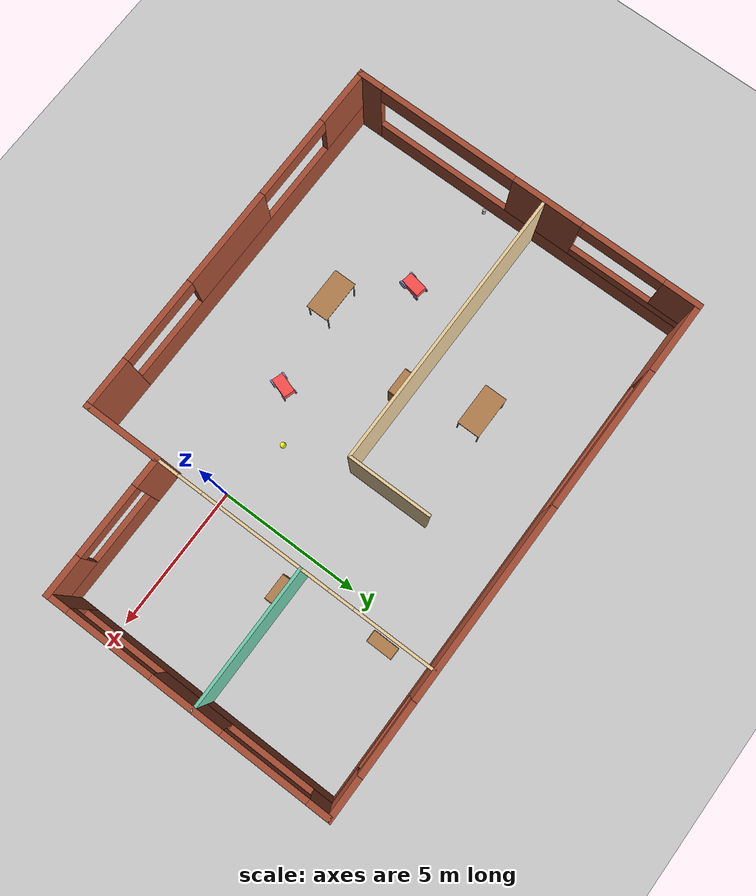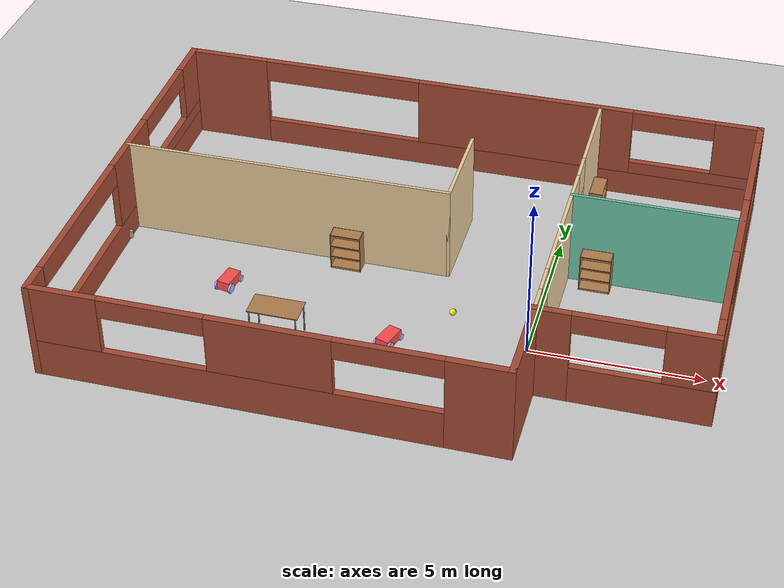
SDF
<sdf version="1.6">
 <world name="default">
  <plugin name="welcome" filename="libwelcome.so"/>
  <light name="sun" type="directional">
   <pose>0 0 10 0 -0 0</pose>
   <diffuse>0.8 0.8 0.8 1</diffuse>
   <specular>0.2 0.2 0.2 1</specular>
   <attenuation>
    <range>1000</range>
    <constant>0.9</constant>
    <linear>0.01</linear>
    <quadratic>0.001</quadratic>
   </attenuation>
   <direction>-0.5 0.1 -0.9</direction>
  </light>
  <model name="ground_plane">
   <static>1</static>
   <link name="link">
    <collision name="collision">
     <geometry><plane><normal>0 0 1</normal><size>100 100</size></plane></geometry>
     <surface>
      <contact><collide_bitmask>65535</collide_bitmask></contact>
      <friction><ode><mu>100</mu><mu2>50</mu2></ode></friction>
     </surface>
    </collision>
    <visual name="visual">
     <cast_shadows>0</cast_shadows>
     <geometry><plane><normal>0 0 1</normal><size>100 100</size></plane></geometry>
     <material>
      <script><uri>file://media/materials/scripts/gazebo.material</uri><name>Gazebo/Grey</name></script>
     </material>
    </visual>
   </link>
  </model>
  <gravity>0 0 -9.8</gravity>
  <magnetic_field>6e-06 2.3e-05 -4.2e-05</magnetic_field>
  <atmosphere type="adiabatic"/>
  <physics name="default_physics" default="0" type="ode">
   <max_step_size>0.001</max_step_size>
   <real_time_factor>1</real_time_factor>
   <real_time_update_rate>1000</real_time_update_rate>
  </physics>
  <scene><ambient>0.4 0.4 0.4 1</ambient><background>0.7 0.7 0.7 1</background><shadows>1</shadows></scene>
  <spherical_coordinates>
   <surface_model>EARTH_WGS84</surface_model>
   <latitude_deg>0</latitude_deg>
   <longitude_deg>0</longitude_deg>
   <elevation>0</elevation>
   <heading_deg>0</heading_deg>
  </spherical_coordinates>
  <model name="bookshelf">
   <static>1</static>
   <link name="link">
    <inertial><mass>1</mass></inertial>
    <collision name="back">
     <pose>0 0.005 0.6 0 -0 0</pose>
     <geometry><box><size>0.9 0.01 1.2</size></box></geometry>
    </collision>
    <visual name="visual1">
     <pose>0 0.005 0.6 0 -0 0</pose>
     <geometry><box><size>0.9 0.01 1.2</size></box></geometry>
     <material>
      <script><uri>file://media/materials/scripts/gazebo.material</uri><name>Gazebo/Wood</name></script>
     </material>
    </visual>
    <collision name="left_side">
     <pose>0.45 -0.195 0.6 0 -0 0</pose>
     <geometry><box><size>0.02 0.4 1.2</size></box></geometry>
    </collision>
    <visual name="visual2">
     <pose>0.45 -0.195 0.6 0 -0 0</pose>
     <geometry><box><size>0.02 0.4 1.2</size></box></geometry>
     <material>
      <script><uri>file://media/materials/scripts/gazebo.material</uri><name>Gazebo/Wood</name></script>
     </material>
    </visual>
    <collision name="right_side">
     <pose>-0.45 -0.195 0.6 0 -0 0</pose>
     <geometry><box><size>0.02 0.4 1.2</size></box></geometry>
    </collision>
    <visual name="visual3">
     <pose>-0.45 -0.195 0.6 0 -0 0</pose>
     <geometry><box><size>0.02 0.4 1.2</size></box></geometry>
     <material>
      <script><uri>file://media/materials/scripts/gazebo.material</uri><name>Gazebo/Wood</name></script>
     </material>
    </visual>
    <collision name="bottom">
     <pose>0 -0.195 0.03 0 -0 0</pose>
     <geometry><box><size>0.88 0.4 0.06</size></box></geometry>
    </collision>
    <visual name="visual4">
     <pose>0 -0.195 0.03 0 -0 0</pose>
     <geometry><box><size>0.88 0.4 0.06</size></box></geometry>
     <material>
      <script><uri>file://media/materials/scripts/gazebo.material</uri><name>Gazebo/Wood</name></script>
     </material>
    </visual>
    <collision name="top">
     <pose>0 -0.195 1.19 0 -0 0</pose>
     <geometry><box><size>0.88 0.4 0.02</size></box></geometry>
    </collision>
    <visual name="visual5">
     <pose>0 -0.195 1.19 0 -0 0</pose>
     <geometry><box><size>0.88 0.4 0.02</size></box></geometry>
     <material>
      <script><uri>file://media/materials/scripts/gazebo.material</uri><name>Gazebo/Wood</name></script>
     </material>
    </visual>
    <collision name="low_shelf">
     <pose>0 -0.195 0.43 0 -0 0</pose>
     <geometry><box><size>0.88 0.4 0.02</size></box></geometry>
    </collision>
    <visual name="visual6">
     <pose>0 -0.195 0.43 0 -0 0</pose>
     <geometry><box><size>0.88 0.4 0.02</size></box></geometry>
     <material>
      <script><uri>file://media/materials/scripts/gazebo.material</uri><name>Gazebo/Wood</name></script>
     </material>
    </visual>
    <collision name="high_shelf">
     <pose>0 -0.195 0.8 0 -0 0</pose>
     <geometry><box><size>0.88 0.4 0.02</size></box></geometry>
    </collision>
    <visual name="visual7">
     <pose>0 -0.195 0.8 0 -0 0</pose>
     <geometry><box><size>0.88 0.4 0.02</size></box></geometry>
     <material>
      <script><uri>file://media/materials/scripts/gazebo.material</uri><name>Gazebo/Wood</name></script>
     </material>
    </visual>
   </link>
   <pose>-5.96108 2.61309 0 0 -0 0</pose>
  </model>
  <model name="beer">
   <link name="link">
    <pose>0 0 0.115 0 -0 0</pose>
    <inertial>
     <mass>0.39</mass>
     <inertia><ixx>0.00058</ixx><ixy>0</ixy><ixz>0</ixz><iyy>0.00058</iyy><iyz>0</iyz><izz>0.00019</izz></inertia>
    </inertial>
    <collision name="collision">
     <geometry><cylinder><radius>0.055</radius><length>0.23</length></cylinder></geometry>
    </collision>
    <visual name="visual">
     <geometry><cylinder><radius>0.055</radius><length>0.23</length></cylinder></geometry>
     <material>
      <script>
       <uri>model://beer/materials/scripts</uri>
       <uri>model://beer/materials/textures</uri>
       <name>Beer/Diffuse</name>
      </script>
     </material>
    </visual>
   </link>
   <pose>-12.2076 1.09427 0.832171 2.9e-05 1.6e-05 0.00079</pose>
  </model>
  <model name="bookshelf_0">
   <static>1</static>
   <link name="link">
    <inertial><mass>1</mass></inertial>
    <collision name="back">
     <pose>0 0.005 0.6 0 -0 0</pose>
     <geometry><box><size>0.9 0.01 1.2</size></box></geometry>
    </collision>
    <visual name="visual1">
     <pose>0 0.005 0.6 0 -0 0</pose>
     <geometry><box><size>0.9 0.01 1.2</size></box></geometry>
     <material>
      <script><uri>file://media/materials/scripts/gazebo.material</uri><name>Gazebo/Wood</name></script>
     </material>
    </visual>
    <collision name="left_side">
     <pose>0.45 -0.195 0.6 0 -0 0</pose>
     <geometry><box><size>0.02 0.4 1.2</size></box></geometry>
    </collision>
    <visual name="visual2">
     <pose>0.45 -0.195 0.6 0 -0 0</pose>
     <geometry><box><size>0.02 0.4 1.2</size></box></geometry>
     <material>
      <script><uri>file://media/materials/scripts/gazebo.material</uri><name>Gazebo/Wood</name></script>
     </material>
    </visual>
    <collision name="right_side">
     <pose>-0.45 -0.195 0.6 0 -0 0</pose>
     <geometry><box><size>0.02 0.4 1.2</size></box></geometry>
    </collision>
    <visual name="visual3">
     <pose>-0.45 -0.195 0.6 0 -0 0</pose>
     <geometry><box><size>0.02 0.4 1.2</size></box></geometry>
     <material>
      <script><uri>file://media/materials/scripts/gazebo.material</uri><name>Gazebo/Wood</name></script>
     </material>
    </visual>
    <collision name="bottom">
     <pose>0 -0.195 0.03 0 -0 0</pose>
     <geometry><box><size>0.88 0.4 0.06</size></box></geometry>
    </collision>
    <visual name="visual4">
     <pose>0 -0.195 0.03 0 -0 0</pose>
     <geometry><box><size>0.88 0.4 0.06</size></box></geometry>
     <material>
      <script><uri>file://media/materials/scripts/gazebo.material</uri><name>Gazebo/Wood</name></script>
     </material>
    </visual>
    <collision name="top">
     <pose>0 -0.195 1.19 0 -0 0</pose>
     <geometry><box><size>0.88 0.4 0.02</size></box></geometry>
    </collision>
    <visual name="visual5">
     <pose>0 -0.195 1.19 0 -0 0</pose>
     <geometry><box><size>0.88 0.4 0.02</size></box></geometry>
     <material>
      <script><uri>file://media/materials/scripts/gazebo.material</uri><name>Gazebo/Wood</name></script>
     </material>
    </visual>
    <collision name="low_shelf">
     <pose>0 -0.195 0.43 0 -0 0</pose>
     <geometry><box><size>0.88 0.4 0.02</size></box></geometry>
    </collision>
    <visual name="visual6">
     <pose>0 -0.195 0.43 0 -0 0</pose>
     <geometry><box><size>0.88 0.4 0.02</size></box></geometry>
     <material>
      <script><uri>file://media/materials/scripts/gazebo.material</uri><name>Gazebo/Wood</name></script>
     </material>
    </visual>
    <collision name="high_shelf">
     <pose>0 -0.195 0.8 0 -0 0</pose>
     <geometry><box><size>0.88 0.4 0.02</size></box></geometry>
    </collision>
    <visual name="visual7">
     <pose>0 -0.195 0.8 0 -0 0</pose>
     <geometry><box><size>0.88 0.4 0.02</size></box></geometry>
     <material>
      <script><uri>file://media/materials/scripts/gazebo.material</uri><name>Gazebo/Wood</name></script>
     </material>
    </visual>
   </link>
   <pose>1.33182 3.46204 0 0 -0 0</pose>
  </model>
  <model name="table">
   <static>1</static>
   <link name="link">
    <collision name="surface">
     <pose>0 0 1 0 -0 0</pose>
     <geometry><box><size>1.5 0.8 0.03</size></box></geometry>
     <surface><friction><ode><mu>0.6</mu><mu2>0.6</mu2></ode></friction></surface>
    </collision>
    <visual name="visual1">
     <pose>0 0 1 0 -0 0</pose>
     <geometry><box><size>1.5 0.8 0.03</size></box></geometry>
     <material>
      <script><uri>file://media/materials/scripts/gazebo.material</uri><name>Gazebo/Wood</name></script>
     </material>
    </visual>
    <collision name="front_left_leg">
     <pose>0.68 0.38 0.5 0 -0 0</pose>
     <geometry><cylinder><radius>0.02</radius><length>1</length></cylinder></geometry>
    </collision>
    <visual name="front_left_leg">
     <pose>0.68 0.38 0.5 0 -0 0</pose>
     <geometry><cylinder><radius>0.02</radius><length>1</length></cylinder></geometry>
     <material>
      <script><uri>file://media/materials/scripts/gazebo.material</uri><name>Gazebo/Grey</name></script>
     </material>
    </visual>
    <collision name="front_right_leg">
     <pose>0.68 -0.38 0.5 0 -0 0</pose>
     <geometry><cylinder><radius>0.02</radius><length>1</length></cylinder></geometry>
    </collision>
    <visual name="front_right_leg">
     <pose>0.68 -0.38 0.5 0 -0 0</pose>
     <geometry><cylinder><radius>0.02</radius><length>1</length></cylinder></geometry>
     <material>
      <script><uri>file://media/materials/scripts/gazebo.material</uri><name>Gazebo/Grey</name></script>
     </material>
    </visual>
    <collision name="back_right_leg">
     <pose>-0.68 -0.38 0.5 0 -0 0</pose>
     <geometry><cylinder><radius>0.02</radius><length>1</length></cylinder></geometry>
    </collision>
    <visual name="back_right_leg">
     <pose>-0.68 -0.38 0.5 0 -0 0</pose>
     <geometry><cylinder><radius>0.02</radius><length>1</length></cylinder></geometry>
     <material>
      <script><uri>file://media/materials/scripts/gazebo.material</uri><name>Gazebo/Grey</name></script>
     </material>
    </visual>
    <collision name="back_left_leg">
     <pose>-0.68 0.38 0.5 0 -0 0</pose>
     <geometry><cylinder><radius>0.02</radius><length>1</length></cylinder></geometry>
    </collision>
    <visual name="back_left_leg">
     <pose>-0.68 0.38 0.5 0 -0 0</pose>
     <geometry><cylinder><radius>0.02</radius><length>1</length></cylinder></geometry>
     <material>
      <script><uri>file://media/materials/scripts/gazebo.material</uri><name>Gazebo/Grey</name></script>
     </material>
    </visual>
   </link>
   <pose>-6.96623 -1.12797 0 0 -0 0</pose>
  </model>
  <model name="bookshelf_1">
   <static>1</static>
   <link name="link">
    <inertial><mass>1</mass></inertial>
    <collision name="back">
     <pose>0 0.005 0.6 0 -0 0</pose>
     <geometry><box><size>0.9 0.01 1.2</size></box></geometry>
    </collision>
    <visual name="visual1">
     <pose>0 0.005 0.6 0 -0 0</pose>
     <geometry><box><size>0.9 0.01 1.2</size></box></geometry>
     <material>
      <script><uri>file://media/materials/scripts/gazebo.material</uri><name>Gazebo/Wood</name></script>
     </material>
    </visual>
    <collision name="left_side">
     <pose>0.45 -0.195 0.6 0 -0 0</pose>
     <geometry><box><size>0.02 0.4 1.2</size></box></geometry>
    </collision>
    <visual name="visual2">
     <pose>0.45 -0.195 0.6 0 -0 0</pose>
     <geometry><box><size>0.02 0.4 1.2</size></box></geometry>
     <material>
      <script><uri>file://media/materials/scripts/gazebo.material</uri><name>Gazebo/Wood</name></script>
     </material>
    </visual>
    <collision name="right_side">
     <pose>-0.45 -0.195 0.6 0 -0 0</pose>
     <geometry><box><size>0.02 0.4 1.2</size></box></geometry>
    </collision>
    <visual name="visual3">
     <pose>-0.45 -0.195 0.6 0 -0 0</pose>
     <geometry><box><size>0.02 0.4 1.2</size></box></geometry>
     <material>
      <script><uri>file://media/materials/scripts/gazebo.material</uri><name>Gazebo/Wood</name></script>
     </material>
    </visual>
    <collision name="bottom">
     <pose>0 -0.195 0.03 0 -0 0</pose>
     <geometry><box><size>0.88 0.4 0.06</size></box></geometry>
    </collision>
    <visual name="visual4">
     <pose>0 -0.195 0.03 0 -0 0</pose>
     <geometry><box><size>0.88 0.4 0.06</size></box></geometry>
     <material>
      <script><uri>file://media/materials/scripts/gazebo.material</uri><name>Gazebo/Wood</name></script>
     </material>
    </visual>
    <collision name="top">
     <pose>0 -0.195 1.19 0 -0 0</pose>
     <geometry><box><size>0.88 0.4 0.02</size></box></geometry>
    </collision>
    <visual name="visual5">
     <pose>0 -0.195 1.19 0 -0 0</pose>
     <geometry><box><size>0.88 0.4 0.02</size></box></geometry>
     <material>
      <script><uri>file://media/materials/scripts/gazebo.material</uri><name>Gazebo/Wood</name></script>
     </material>
    </visual>
    <collision name="low_shelf">
     <pose>0 -0.195 0.43 0 -0 0</pose>
     <geometry><box><size>0.88 0.4 0.02</size></box></geometry>
    </collision>
    <visual name="visual6">
     <pose>0 -0.195 0.43 0 -0 0</pose>
     <geometry><box><size>0.88 0.4 0.02</size></box></geometry>
     <material>
      <script><uri>file://media/materials/scripts/gazebo.material</uri><name>Gazebo/Wood</name></script>
     </material>
    </visual>
    <collision name="high_shelf">
     <pose>0 -0.195 0.8 0 -0 0</pose>
     <geometry><box><size>0.88 0.4 0.02</size></box></geometry>
    </collision>
    <visual name="visual7">
     <pose>0 -0.195 0.8 0 -0 0</pose>
     <geometry><box><size>0.88 0.4 0.02</size></box></geometry>
     <material>
      <script><uri>file://media/materials/scripts/gazebo.material</uri><name>Gazebo/Wood</name></script>
     </material>
    </visual>
   </link>
   <pose>0.564045 6.70754 0 0 -0 1.56615</pose>
  </model>
  <model name="table_0">
   <static>1</static>
   <link name="link">
    <collision name="surface">
     <pose>0 0 1 0 -0 0</pose>
     <geometry><box><size>1.5 0.8 0.03</size></box></geometry>
     <surface><friction><ode><mu>0.6</mu><mu2>0.6</mu2></ode></friction></surface>
    </collision>
    <visual name="visual1">
     <pose>0 0 1 0 -0 0</pose>
     <geometry><box><size>1.5 0.8 0.03</size></box></geometry>
     <material>
      <script><uri>file://media/materials/scripts/gazebo.material</uri><name>Gazebo/Wood</name></script>
     </material>
    </visual>
    <collision name="front_left_leg">
     <pose>0.68 0.38 0.5 0 -0 0</pose>
     <geometry><cylinder><radius>0.02</radius><length>1</length></cylinder></geometry>
    </collision>
    <visual name="front_left_leg">
     <pose>0.68 0.38 0.5 0 -0 0</pose>
     <geometry><cylinder><radius>0.02</radius><length>1</length></cylinder></geometry>
     <material>
      <script><uri>file://media/materials/scripts/gazebo.material</uri><name>Gazebo/Grey</name></script>
     </material>
    </visual>
    <collision name="front_right_leg">
     <pose>0.68 -0.38 0.5 0 -0 0</pose>
     <geometry><cylinder><radius>0.02</radius><length>1</length></cylinder></geometry>
    </collision>
    <visual name="front_right_leg">
     <pose>0.68 -0.38 0.5 0 -0 0</pose>
     <geometry><cylinder><radius>0.02</radius><length>1</length></cylinder></geometry>
     <material>
      <script><uri>file://media/materials/scripts/gazebo.material</uri><name>Gazebo/Grey</name></script>
     </material>
    </visual>
    <collision name="back_right_leg">
     <pose>-0.68 -0.38 0.5 0 -0 0</pose>
     <geometry><cylinder><radius>0.02</radius><length>1</length></cylinder></geometry>
    </collision>
    <visual name="back_right_leg">
     <pose>-0.68 -0.38 0.5 0 -0 0</pose>
     <geometry><cylinder><radius>0.02</radius><length>1</length></cylinder></geometry>
     <material>
      <script><uri>file://media/materials/scripts/gazebo.material</uri><name>Gazebo/Grey</name></script>
     </material>
    </visual>
    <collision name="back_left_leg">
     <pose>-0.68 0.38 0.5 0 -0 0</pose>
     <geometry><cylinder><radius>0.02</radius><length>1</length></cylinder></geometry>
    </collision>
    <visual name="back_left_leg">
     <pose>-0.68 0.38 0.5 0 -0 0</pose>
     <geometry><cylinder><radius>0.02</radius><length>1</length></cylinder></geometry>
     <material>
      <script><uri>file://media/materials/scripts/gazebo.material</uri><name>Gazebo/Grey</name></script>
     </material>
    </visual>
   </link>
   <pose>-6.78918 4.91464 0 0 -0 0</pose>
  </model>
  <model name="Robot">
   <link name="link_0">
    <pose>0 -0.02 0.06 0 -0 0</pose>
    <inertial>
     <mass>1</mass>
     <inertia>
      <ixx>0.166667</ixx>
      <ixy>0</ixy>
      <ixz>0</ixz>
      <iyy>0.166667</iyy>
      <iyz>0</iyz>
      <izz>0.166667</izz>
     </inertia>
    </inertial>
    <visual name="visual">
     <geometry><box><size>0.4 0.7 0.3</size></box></geometry>
     <material>
      <lighting>1</lighting>
      <script><uri>file://media/materials/scripts/gazebo.material</uri><name>Gazebo/Grey</name></script>
      <shader type="pixel"><normal_map>__default__</normal_map></shader>
      <ambient>1 0.3 0.3 1</ambient>
      <diffuse>0.7 0.7 0.7 1</diffuse>
      <specular>0.01 0.01 0.01 1</specular>
      <emissive>0 0 0 1</emissive>
     </material>
    </visual>
    <collision name="collision">
     <geometry><box><size>0.4 0.7 0.3</size></box></geometry>
     <surface>
      <friction>
       <ode><mu>1</mu><mu2>1</mu2><fdir1>0 0 0</fdir1><slip1>0</slip1><slip2>0</slip2></ode>
       <torsional>
        <coefficient>1</coefficient>
        <patch_radius>0</patch_radius>
        <surface_radius>0</surface_radius>
        <use_patch_radius>1</use_patch_radius>
        <ode><slip>0</slip></ode>
       </torsional>
      </friction>
      <bounce><restitution_coefficient>0</restitution_coefficient><threshold>1e+06</threshold></bounce>
      <contact>
       <collide_without_contact>0</collide_without_contact>
       <collide_without_contact_bitmask>1</collide_without_contact_bitmask>
       <collide_bitmask>1</collide_bitmask>
       <ode>
        <soft_cfm>0</soft_cfm>
        <soft_erp>0.2</soft_erp>
        <kp>1e+13</kp>
        <kd>1</kd>
        <max_vel>0.01</max_vel>
        <min_depth>0</min_depth>
       </ode>
       <bullet>
        <split_impulse>1</split_impulse>
        <split_impulse_penetration_threshold>-0.01</split_impulse_penetration_threshold>
        <soft_cfm>0</soft_cfm>
        <soft_erp>0.2</soft_erp>
        <kp>1e+13</kp>
        <kd>1</kd>
       </bullet>
      </contact>
     </surface>
    </collision>
   </link>
   <link name="link_1">
    <pose>-0.215 0.3 -0.04 0 -0 0</pose>
    <inertial>
     <mass>1</mass>
     <inertia><ixx>0.145833</ixx><ixy>0</ixy><ixz>0</ixz><iyy>0.145833</iyy><iyz>0</iyz><izz>0.125</izz></inertia>
    </inertial>
    <visual name="visual">
     <pose>0 0 0 1.5708 -0 1.5708</pose>
     <geometry><cylinder><radius>0.1</radius><length>0.03</length></cylinder></geometry>
     <material>
      <lighting>1</lighting>
      <script><uri>file://media/materials/scripts/gazebo.material</uri><name>Gazebo/Grey</name></script>
      <shader type="pixel"><normal_map>__default__</normal_map></shader>
      <ambient>0.3 0.3 1 1</ambient>
      <diffuse>0.7 0.7 1 1</diffuse>
      <specular>0.01 0.01 0.01 1</specular>
      <emissive>0 0 0 1</emissive>
     </material>
    </visual>
    <collision name="collision">
     <pose>0 0 0 1.5708 -0 1.5708</pose>
     <geometry><cylinder><radius>0.1</radius><length>0.03</length></cylinder></geometry>
     <surface>
      <friction>
       <ode><mu>1</mu><mu2>1</mu2><fdir1>0 0 0</fdir1><slip1>0</slip1><slip2>0</slip2></ode>
       <torsional>
        <coefficient>1</coefficient>
        <patch_radius>0</patch_radius>
        <surface_radius>0</surface_radius>
        <use_patch_radius>1</use_patch_radius>
        <ode><slip>0</slip></ode>
       </torsional>
      </friction>
      <bounce><restitution_coefficient>0</restitution_coefficient><threshold>1e+06</threshold></bounce>
      <contact>
       <collide_without_contact>0</collide_without_contact>
       <collide_without_contact_bitmask>1</collide_without_contact_bitmask>
       <collide_bitmask>1</collide_bitmask>
       <ode>
        <soft_cfm>0</soft_cfm>
        <soft_erp>0.2</soft_erp>
        <kp>1e+13</kp>
        <kd>1</kd>
        <max_vel>0.01</max_vel>
        <min_depth>0</min_depth>
       </ode>
       <bullet>
        <split_impulse>1</split_impulse>
        <split_impulse_penetration_threshold>-0.01</split_impulse_penetration_threshold>
        <soft_cfm>0</soft_cfm>
        <soft_erp>0.2</soft_erp>
        <kp>1e+13</kp>
        <kd>1</kd>
       </bullet>
      </contact>
     </surface>
    </collision>
   </link>
   <link name="link_1_clone">
    <pose>0.215 0.3 -0.04 0 -0 0</pose>
    <inertial>
     <mass>1</mass>
     <inertia><ixx>0.145833</ixx><ixy>0</ixy><ixz>0</ixz><iyy>0.145833</iyy><iyz>0</iyz><izz>0.125</izz></inertia>
    </inertial>
    <visual name="visual">
     <pose>0 0 0 1.5708 -0 1.5708</pose>
     <geometry><cylinder><radius>0.1</radius><length>0.03</length></cylinder></geometry>
     <material>
      <lighting>1</lighting>
      <script><uri>file://media/materials/scripts/gazebo.material</uri><name>Gazebo/Grey</name></script>
      <shader type="pixel"><normal_map>__default__</normal_map></shader>
      <ambient>0.3 0.3 1 1</ambient>
      <diffuse>0.7 0.7 1 1</diffuse>
      <specular>0.01 0.01 0.01 1</specular>
      <emissive>0 0 0 1</emissive>
     </material>
    </visual>
    <collision name="collision">
     <pose>0 0 0 1.5708 -0 1.5708</pose>
     <geometry><cylinder><radius>0.1</radius><length>0.03</length></cylinder></geometry>
     <surface>
      <friction>
       <ode><mu>1</mu><mu2>1</mu2><fdir1>0 0 0</fdir1><slip1>0</slip1><slip2>0</slip2></ode>
       <torsional>
        <coefficient>1</coefficient>
        <patch_radius>0</patch_radius>
        <surface_radius>0</surface_radius>
        <use_patch_radius>1</use_patch_radius>
        <ode><slip>0</slip></ode>
       </torsional>
      </friction>
      <bounce><restitution_coefficient>0</restitution_coefficient><threshold>1e+06</threshold></bounce>
      <contact>
       <collide_without_contact>0</collide_without_contact>
       <collide_without_contact_bitmask>1</collide_without_contact_bitmask>
       <collide_bitmask>1</collide_bitmask>
       <ode>
        <soft_cfm>0</soft_cfm>
        <soft_erp>0.2</soft_erp>
        <kp>1e+13</kp>
        <kd>1</kd>
        <max_vel>0.01</max_vel>
        <min_depth>0</min_depth>
       </ode>
       <bullet>
        <split_impulse>1</split_impulse>
        <split_impulse_penetration_threshold>-0.01</split_impulse_penetration_threshold>
        <soft_cfm>0</soft_cfm>
        <soft_erp>0.2</soft_erp>
        <kp>1e+13</kp>
        <kd>1</kd>
       </bullet>
      </contact>
     </surface>
    </collision>
   </link>
   <link name="link_1_clone_clone">
    <pose>-0.225 -0.29 0.01 0 -0 0</pose>
    <inertial>
     <mass>1</mass>
     <inertia><ixx>0.145833</ixx><ixy>0</ixy><ixz>0</ixz><iyy>0.145833</iyy><iyz>0</iyz><izz>0.125</izz></inertia>
    </inertial>
    <visual name="visual">
     <pose>0 0 0 1.5708 -0 1.5708</pose>
     <geometry><cylinder><radius>0.15</radius><length>0.05</length></cylinder></geometry>
     <material>
      <lighting>1</lighting>
      <script><uri>file://media/materials/scripts/gazebo.material</uri><name>Gazebo/Grey</name></script>
      <shader type="pixel"><normal_map>__default__</normal_map></shader>
      <ambient>0.3 0.3 1 1</ambient>
      <diffuse>0.7 0.7 1 1</diffuse>
      <specular>0.01 0.01 0.01 1</specular>
      <emissive>0 0 0 1</emissive>
     </material>
    </visual>
    <collision name="collision">
     <pose>0 0 0 1.5708 -0 1.5708</pose>
     <geometry><cylinder><radius>0.15</radius><length>0.05</length></cylinder></geometry>
     <surface>
      <friction>
       <ode><mu>1</mu><mu2>1</mu2><fdir1>0 0 0</fdir1><slip1>0</slip1><slip2>0</slip2></ode>
       <torsional>
        <coefficient>1</coefficient>
        <patch_radius>0</patch_radius>
        <surface_radius>0</surface_radius>
        <use_patch_radius>1</use_patch_radius>
        <ode><slip>0</slip></ode>
       </torsional>
      </friction>
      <bounce><restitution_coefficient>0</restitution_coefficient><threshold>1e+06</threshold></bounce>
      <contact>
       <collide_without_contact>0</collide_without_contact>
       <collide_without_contact_bitmask>1</collide_without_contact_bitmask>
       <collide_bitmask>1</collide_bitmask>
       <ode>
        <soft_cfm>0</soft_cfm>
        <soft_erp>0.2</soft_erp>
        <kp>1e+13</kp>
        <kd>1</kd>
        <max_vel>0.01</max_vel>
        <min_depth>0</min_depth>
       </ode>
       <bullet>
        <split_impulse>1</split_impulse>
        <split_impulse_penetration_threshold>-0.01</split_impulse_penetration_threshold>
        <soft_cfm>0</soft_cfm>
        <soft_erp>0.2</soft_erp>
        <kp>1e+13</kp>
        <kd>1</kd>
       </bullet>
      </contact>
     </surface>
    </collision>
   </link>
   <link name="link_1_clone_clone_clone">
    <pose>0.225 -0.29 0.01 0 -0 0</pose>
    <inertial>
     <mass>1</mass>
     <inertia><ixx>0.145833</ixx><ixy>0</ixy><ixz>0</ixz><iyy>0.145833</iyy><iyz>0</iyz><izz>0.125</izz></inertia>
    </inertial>
    <visual name="visual">
     <pose>0 0 0 1.5708 -0 1.5708</pose>
     <geometry><cylinder><radius>0.15</radius><length>0.05</length></cylinder></geometry>
     <material>
      <lighting>1</lighting>
      <script><uri>file://media/materials/scripts/gazebo.material</uri><name>Gazebo/Grey</name></script>
      <shader type="pixel"><normal_map>__default__</normal_map></shader>
      <ambient>0.3 0.3 1 1</ambient>
      <diffuse>0.7 0.7 1 1</diffuse>
      <specular>0.01 0.01 0.01 1</specular>
      <emissive>0 0 0 1</emissive>
     </material>
    </visual>
    <collision name="collision">
     <pose>0 0 0 1.5708 -0 1.5708</pose>
     <geometry><cylinder><radius>0.15</radius><length>0.05</length></cylinder></geometry>
     <surface>
      <friction>
       <ode><mu>1</mu><mu2>1</mu2><fdir1>0 0 0</fdir1><slip1>0</slip1><slip2>0</slip2></ode>
       <torsional>
        <coefficient>1</coefficient>
        <patch_radius>0</patch_radius>
        <surface_radius>0</surface_radius>
        <use_patch_radius>1</use_patch_radius>
        <ode><slip>0</slip></ode>
       </torsional>
      </friction>
      <bounce><restitution_coefficient>0</restitution_coefficient><threshold>1e+06</threshold></bounce>
      <contact>
       <collide_without_contact>0</collide_without_contact>
       <collide_without_contact_bitmask>1</collide_without_contact_bitmask>
       <collide_bitmask>1</collide_bitmask>
       <ode>
        <soft_cfm>0</soft_cfm>
        <soft_erp>0.2</soft_erp>
        <kp>1e+13</kp>
        <kd>1</kd>
        <max_vel>0.01</max_vel>
        <min_depth>0</min_depth>
       </ode>
       <bullet>
        <split_impulse>1</split_impulse>
        <split_impulse_penetration_threshold>-0.01</split_impulse_penetration_threshold>
        <soft_cfm>0</soft_cfm>
        <soft_erp>0.2</soft_erp>
        <kp>1e+13</kp>
        <kd>1</kd>
       </bullet>
      </contact>
     </surface>
    </collision>
   </link>
   <joint name="link_0_JOINT_0" type="revolute">
    <parent>link_0</parent>
    <child>link_1</child>
    <axis>
     <xyz>-1 0 0</xyz>
     <use_parent_model_frame>0</use_parent_model_frame>
     <limit>
      <lower>-1.79769e+308</lower>
      <upper>1.79769e+308</upper>
      <effort>-1</effort>
      <velocity>-1</velocity>
     </limit>
     <dynamics>
      <spring_reference>0</spring_reference>
      <spring_stiffness>0</spring_stiffness>
      <damping>0</damping>
      <friction>0</friction>
     </dynamics>
    </axis>
    <physics>
     <ode><limit><cfm>0</cfm><erp>0.2</erp></limit><suspension><cfm>0</cfm><erp>0.2</erp></suspension></ode>
    </physics>
   </joint>
   <joint name="link_0_JOINT_1" type="revolute">
    <parent>link_0</parent>
    <child>link_1_clone</child>
    <axis>
     <xyz>-1 0 0</xyz>
     <use_parent_model_frame>0</use_parent_model_frame>
     <limit>
      <lower>-1.79769e+308</lower>
      <upper>1.79769e+308</upper>
      <effort>-1</effort>
      <velocity>-1</velocity>
     </limit>
     <dynamics>
      <spring_reference>0</spring_reference>
      <spring_stiffness>0</spring_stiffness>
      <damping>0</damping>
      <friction>0</friction>
     </dynamics>
    </axis>
    <physics>
     <ode><limit><cfm>0</cfm><erp>0.2</erp></limit><suspension><cfm>0</cfm><erp>0.2</erp></suspension></ode>
    </physics>
   </joint>
   <joint name="link_0_JOINT_3" type="revolute">
    <parent>link_0</parent>
    <child>link_1_clone_clone</child>
    <axis>
     <xyz>-1 0 0</xyz>
     <use_parent_model_frame>0</use_parent_model_frame>
     <limit>
      <lower>-1.79769e+308</lower>
      <upper>1.79769e+308</upper>
      <effort>-1</effort>
      <velocity>-1</velocity>
     </limit>
     <dynamics>
      <spring_reference>0</spring_reference>
      <spring_stiffness>0</spring_stiffness>
      <damping>0</damping>
      <friction>0</friction>
     </dynamics>
    </axis>
    <physics>
     <ode><limit><cfm>0</cfm><erp>0.2</erp></limit><suspension><cfm>0</cfm><erp>0.2</erp></suspension></ode>
    </physics>
   </joint>
   <joint name="link_0_JOINT_4" type="revolute">
    <parent>link_0</parent>
    <child>link_1_clone_clone_clone</child>
    <axis>
     <xyz>1 0 0</xyz>
     <use_parent_model_frame>0</use_parent_model_frame>
     <limit>
      <lower>-1.79769e+308</lower>
      <upper>1.79769e+308</upper>
      <effort>-1</effort>
      <velocity>-1</velocity>
     </limit>
     <dynamics>
      <spring_reference>0</spring_reference>
      <spring_stiffness>0</spring_stiffness>
      <damping>0</damping>
      <friction>0</friction>
     </dynamics>
    </axis>
    <physics>
     <ode><limit><cfm>0</cfm><erp>0.2</erp></limit><suspension><cfm>0</cfm><erp>0.2</erp></suspension></ode>
    </physics>
   </joint>
   <static>0</static>
   <pose>-9.03567 0.657132 0.14 0 0 -0.185466</pose>
  </model>
  <model name="Robot_0">
   <link name="link_0">
    <pose>0 -0.02 0.06 0 -0 0</pose>
    <inertial>
     <mass>1</mass>
     <inertia>
      <ixx>0.166667</ixx>
      <ixy>0</ixy>
      <ixz>0</ixz>
      <iyy>0.166667</iyy>
      <iyz>0</iyz>
      <izz>0.166667</izz>
     </inertia>
    </inertial>
    <visual name="visual">
     <geometry><box><size>0.4 0.7 0.3</size></box></geometry>
     <material>
      <lighting>1</lighting>
      <script><uri>file://media/materials/scripts/gazebo.material</uri><name>Gazebo/Grey</name></script>
      <shader type="pixel"><normal_map>__default__</normal_map></shader>
      <ambient>1 0.3 0.3 1</ambient>
      <diffuse>0.7 0.7 0.7 1</diffuse>
      <specular>0.01 0.01 0.01 1</specular>
      <emissive>0 0 0 1</emissive>
     </material>
    </visual>
    <collision name="collision">
     <geometry><box><size>0.4 0.7 0.3</size></box></geometry>
     <surface>
      <friction>
       <ode><mu>1</mu><mu2>1</mu2><fdir1>0 0 0</fdir1><slip1>0</slip1><slip2>0</slip2></ode>
       <torsional>
        <coefficient>1</coefficient>
        <patch_radius>0</patch_radius>
        <surface_radius>0</surface_radius>
        <use_patch_radius>1</use_patch_radius>
        <ode><slip>0</slip></ode>
       </torsional>
      </friction>
      <bounce><restitution_coefficient>0</restitution_coefficient><threshold>1e+06</threshold></bounce>
      <contact>
       <collide_without_contact>0</collide_without_contact>
       <collide_without_contact_bitmask>1</collide_without_contact_bitmask>
       <collide_bitmask>1</collide_bitmask>
       <ode>
        <soft_cfm>0</soft_cfm>
        <soft_erp>0.2</soft_erp>
        <kp>1e+13</kp>
        <kd>1</kd>
        <max_vel>0.01</max_vel>
        <min_depth>0</min_depth>
       </ode>
       <bullet>
        <split_impulse>1</split_impulse>
        <split_impulse_penetration_threshold>-0.01</split_impulse_penetration_threshold>
        <soft_cfm>0</soft_cfm>
        <soft_erp>0.2</soft_erp>
        <kp>1e+13</kp>
        <kd>1</kd>
       </bullet>
      </contact>
     </surface>
    </collision>
   </link>
   <link name="link_1">
    <pose>-0.215 0.3 -0.04 0 -0 0</pose>
    <inertial>
     <mass>1</mass>
     <inertia><ixx>0.145833</ixx><ixy>0</ixy><ixz>0</ixz><iyy>0.145833</iyy><iyz>0</iyz><izz>0.125</izz></inertia>
    </inertial>
    <visual name="visual">
     <pose>0 0 0 1.5708 -0 1.5708</pose>
     <geometry><cylinder><radius>0.1</radius><length>0.03</length></cylinder></geometry>
     <material>
      <lighting>1</lighting>
      <script><uri>file://media/materials/scripts/gazebo.material</uri><name>Gazebo/Grey</name></script>
      <shader type="pixel"><normal_map>__default__</normal_map></shader>
      <ambient>0.3 0.3 1 1</ambient>
      <diffuse>0.7 0.7 1 1</diffuse>
      <specular>0.01 0.01 0.01 1</specular>
      <emissive>0 0 0 1</emissive>
     </material>
    </visual>
    <collision name="collision">
     <pose>0 0 0 1.5708 -0 1.5708</pose>
     <geometry><cylinder><radius>0.1</radius><length>0.03</length></cylinder></geometry>
     <surface>
      <friction>
       <ode><mu>1</mu><mu2>1</mu2><fdir1>0 0 0</fdir1><slip1>0</slip1><slip2>0</slip2></ode>
       <torsional>
        <coefficient>1</coefficient>
        <patch_radius>0</patch_radius>
        <surface_radius>0</surface_radius>
        <use_patch_radius>1</use_patch_radius>
        <ode><slip>0</slip></ode>
       </torsional>
      </friction>
      <bounce><restitution_coefficient>0</restitution_coefficient><threshold>1e+06</threshold></bounce>
      <contact>
       <collide_without_contact>0</collide_without_contact>
       <collide_without_contact_bitmask>1</collide_without_contact_bitmask>
       <collide_bitmask>1</collide_bitmask>
       <ode>
        <soft_cfm>0</soft_cfm>
        <soft_erp>0.2</soft_erp>
        <kp>1e+13</kp>
        <kd>1</kd>
        <max_vel>0.01</max_vel>
        <min_depth>0</min_depth>
       </ode>
       <bullet>
        <split_impulse>1</split_impulse>
        <split_impulse_penetration_threshold>-0.01</split_impulse_penetration_threshold>
        <soft_cfm>0</soft_cfm>
        <soft_erp>0.2</soft_erp>
        <kp>1e+13</kp>
        <kd>1</kd>
       </bullet>
      </contact>
     </surface>
    </collision>
   </link>
   <link name="link_1_clone">
    <pose>0.215 0.3 -0.04 0 -0 0</pose>
    <inertial>
     <mass>1</mass>
     <inertia><ixx>0.145833</ixx><ixy>0</ixy><ixz>0</ixz><iyy>0.145833</iyy><iyz>0</iyz><izz>0.125</izz></inertia>
    </inertial>
    <visual name="visual">
     <pose>0 0 0 1.5708 -0 1.5708</pose>
     <geometry><cylinder><radius>0.1</radius><length>0.03</length></cylinder></geometry>
     <material>
      <lighting>1</lighting>
      <script><uri>file://media/materials/scripts/gazebo.material</uri><name>Gazebo/Grey</name></script>
      <shader type="pixel"><normal_map>__default__</normal_map></shader>
      <ambient>0.3 0.3 1 1</ambient>
      <diffuse>0.7 0.7 1 1</diffuse>
      <specular>0.01 0.01 0.01 1</specular>
      <emissive>0 0 0 1</emissive>
     </material>
    </visual>
    <collision name="collision">
     <pose>0 0 0 1.5708 -0 1.5708</pose>
     <geometry><cylinder><radius>0.1</radius><length>0.03</length></cylinder></geometry>
     <surface>
      <friction>
       <ode><mu>1</mu><mu2>1</mu2><fdir1>0 0 0</fdir1><slip1>0</slip1><slip2>0</slip2></ode>
       <torsional>
        <coefficient>1</coefficient>
        <patch_radius>0</patch_radius>
        <surface_radius>0</surface_radius>
        <use_patch_radius>1</use_patch_radius>
        <ode><slip>0</slip></ode>
       </torsional>
      </friction>
      <bounce><restitution_coefficient>0</restitution_coefficient><threshold>1e+06</threshold></bounce>
      <contact>
       <collide_without_contact>0</collide_without_contact>
       <collide_without_contact_bitmask>1</collide_without_contact_bitmask>
       <collide_bitmask>1</collide_bitmask>
       <ode>
        <soft_cfm>0</soft_cfm>
        <soft_erp>0.2</soft_erp>
        <kp>1e+13</kp>
        <kd>1</kd>
        <max_vel>0.01</max_vel>
        <min_depth>0</min_depth>
       </ode>
       <bullet>
        <split_impulse>1</split_impulse>
        <split_impulse_penetration_threshold>-0.01</split_impulse_penetration_threshold>
        <soft_cfm>0</soft_cfm>
        <soft_erp>0.2</soft_erp>
        <kp>1e+13</kp>
        <kd>1</kd>
       </bullet>
      </contact>
     </surface>
    </collision>
   </link>
   <link name="link_1_clone_clone">
    <pose>-0.225 -0.29 0.01 0 -0 0</pose>
    <inertial>
     <mass>1</mass>
     <inertia><ixx>0.145833</ixx><ixy>0</ixy><ixz>0</ixz><iyy>0.145833</iyy><iyz>0</iyz><izz>0.125</izz></inertia>
    </inertial>
    <visual name="visual">
     <pose>0 0 0 1.5708 -0 1.5708</pose>
     <geometry><cylinder><radius>0.15</radius><length>0.05</length></cylinder></geometry>
     <material>
      <lighting>1</lighting>
      <script><uri>file://media/materials/scripts/gazebo.material</uri><name>Gazebo/Grey</name></script>
      <shader type="pixel"><normal_map>__default__</normal_map></shader>
      <ambient>0.3 0.3 1 1</ambient>
      <diffuse>0.7 0.7 1 1</diffuse>
      <specular>0.01 0.01 0.01 1</specular>
      <emissive>0 0 0 1</emissive>
     </material>
    </visual>
    <collision name="collision">
     <pose>0 0 0 1.5708 -0 1.5708</pose>
     <geometry><cylinder><radius>0.15</radius><length>0.05</length></cylinder></geometry>
     <surface>
      <friction>
       <ode><mu>1</mu><mu2>1</mu2><fdir1>0 0 0</fdir1><slip1>0</slip1><slip2>0</slip2></ode>
       <torsional>
        <coefficient>1</coefficient>
        <patch_radius>0</patch_radius>
        <surface_radius>0</surface_radius>
        <use_patch_radius>1</use_patch_radius>
        <ode><slip>0</slip></ode>
       </torsional>
      </friction>
      <bounce><restitution_coefficient>0</restitution_coefficient><threshold>1e+06</threshold></bounce>
      <contact>
       <collide_without_contact>0</collide_without_contact>
       <collide_without_contact_bitmask>1</collide_without_contact_bitmask>
       <collide_bitmask>1</collide_bitmask>
       <ode>
        <soft_cfm>0</soft_cfm>
        <soft_erp>0.2</soft_erp>
        <kp>1e+13</kp>
        <kd>1</kd>
        <max_vel>0.01</max_vel>
        <min_depth>0</min_depth>
       </ode>
       <bullet>
        <split_impulse>1</split_impulse>
        <split_impulse_penetration_threshold>-0.01</split_impulse_penetration_threshold>
        <soft_cfm>0</soft_cfm>
        <soft_erp>0.2</soft_erp>
        <kp>1e+13</kp>
        <kd>1</kd>
       </bullet>
      </contact>
     </surface>
    </collision>
   </link>
   <link name="link_1_clone_clone_clone">
    <pose>0.225 -0.29 0.01 0 -0 0</pose>
    <inertial>
     <mass>1</mass>
     <inertia><ixx>0.145833</ixx><ixy>0</ixy><ixz>0</ixz><iyy>0.145833</iyy><iyz>0</iyz><izz>0.125</izz></inertia>
    </inertial>
    <visual name="visual">
     <pose>0 0 0 1.5708 -0 1.5708</pose>
     <geometry><cylinder><radius>0.15</radius><length>0.05</length></cylinder></geometry>
     <material>
      <lighting>1</lighting>
      <script><uri>file://media/materials/scripts/gazebo.material</uri><name>Gazebo/Grey</name></script>
      <shader type="pixel"><normal_map>__default__</normal_map></shader>
      <ambient>0.3 0.3 1 1</ambient>
      <diffuse>0.7 0.7 1 1</diffuse>
      <specular>0.01 0.01 0.01 1</specular>
      <emissive>0 0 0 1</emissive>
     </material>
    </visual>
    <collision name="collision">
     <pose>0 0 0 1.5708 -0 1.5708</pose>
     <geometry><cylinder><radius>0.15</radius><length>0.05</length></cylinder></geometry>
     <surface>
      <friction>
       <ode><mu>1</mu><mu2>1</mu2><fdir1>0 0 0</fdir1><slip1>0</slip1><slip2>0</slip2></ode>
       <torsional>
        <coefficient>1</coefficient>
        <patch_radius>0</patch_radius>
        <surface_radius>0</surface_radius>
        <use_patch_radius>1</use_patch_radius>
        <ode><slip>0</slip></ode>
       </torsional>
      </friction>
      <bounce><restitution_coefficient>0</restitution_coefficient><threshold>1e+06</threshold></bounce>
      <contact>
       <collide_without_contact>0</collide_without_contact>
       <collide_without_contact_bitmask>1</collide_without_contact_bitmask>
       <collide_bitmask>1</collide_bitmask>
       <ode>
        <soft_cfm>0</soft_cfm>
        <soft_erp>0.2</soft_erp>
        <kp>1e+13</kp>
        <kd>1</kd>
        <max_vel>0.01</max_vel>
        <min_depth>0</min_depth>
       </ode>
       <bullet>
        <split_impulse>1</split_impulse>
        <split_impulse_penetration_threshold>-0.01</split_impulse_penetration_threshold>
        <soft_cfm>0</soft_cfm>
        <soft_erp>0.2</soft_erp>
        <kp>1e+13</kp>
        <kd>1</kd>
       </bullet>
      </contact>
     </surface>
    </collision>
   </link>
   <joint name="link_0_JOINT_0" type="revolute">
    <parent>link_0</parent>
    <child>link_1</child>
    <axis>
     <xyz>-1 0 0</xyz>
     <use_parent_model_frame>0</use_parent_model_frame>
     <limit>
      <lower>-1.79769e+308</lower>
      <upper>1.79769e+308</upper>
      <effort>-1</effort>
      <velocity>-1</velocity>
     </limit>
     <dynamics>
      <spring_reference>0</spring_reference>
      <spring_stiffness>0</spring_stiffness>
      <damping>0</damping>
      <friction>0</friction>
     </dynamics>
    </axis>
    <physics>
     <ode><limit><cfm>0</cfm><erp>0.2</erp></limit><suspension><cfm>0</cfm><erp>0.2</erp></suspension></ode>
    </physics>
   </joint>
   <joint name="link_0_JOINT_1" type="revolute">
    <parent>link_0</parent>
    <child>link_1_clone</child>
    <axis>
     <xyz>-1 0 0</xyz>
     <use_parent_model_frame>0</use_parent_model_frame>
     <limit>
      <lower>-1.79769e+308</lower>
      <upper>1.79769e+308</upper>
      <effort>-1</effort>
      <velocity>-1</velocity>
     </limit>
     <dynamics>
      <spring_reference>0</spring_reference>
      <spring_stiffness>0</spring_stiffness>
      <damping>0</damping>
      <friction>0</friction>
     </dynamics>
    </axis>
    <physics>
     <ode><limit><cfm>0</cfm><erp>0.2</erp></limit><suspension><cfm>0</cfm><erp>0.2</erp></suspension></ode>
    </physics>
   </joint>
   <joint name="link_0_JOINT_3" type="revolute">
    <parent>link_0</parent>
    <child>link_1_clone_clone</child>
    <axis>
     <xyz>-1 0 0</xyz>
     <use_parent_model_frame>0</use_parent_model_frame>
     <limit>
      <lower>-1.79769e+308</lower>
      <upper>1.79769e+308</upper>
      <effort>-1</effort>
      <velocity>-1</velocity>
     </limit>
     <dynamics>
      <spring_reference>0</spring_reference>
      <spring_stiffness>0</spring_stiffness>
      <damping>0</damping>
      <friction>0</friction>
     </dynamics>
    </axis>
    <physics>
     <ode><limit><cfm>0</cfm><erp>0.2</erp></limit><suspension><cfm>0</cfm><erp>0.2</erp></suspension></ode>
    </physics>
   </joint>
   <joint name="link_0_JOINT_4" type="revolute">
    <parent>link_0</parent>
    <child>link_1_clone_clone_clone</child>
    <axis>
     <xyz>1 0 0</xyz>
     <use_parent_model_frame>0</use_parent_model_frame>
     <limit>
      <lower>-1.79769e+308</lower>
      <upper>1.79769e+308</upper>
      <effort>-1</effort>
      <velocity>-1</velocity>
     </limit>
     <dynamics>
      <spring_reference>0</spring_reference>
      <spring_stiffness>0</spring_stiffness>
      <damping>0</damping>
      <friction>0</friction>
     </dynamics>
    </axis>
    <physics>
     <ode><limit><cfm>0</cfm><erp>0.2</erp></limit><suspension><cfm>0</cfm><erp>0.2</erp></suspension></ode>
    </physics>
   </joint>
   <static>0</static>
   <pose>-3.81595 -0.679022 0.14 0 0 -0.310188</pose>
  </model>
  <model name="new_building">
   <pose>-3.75518 2.01418 0 0 -0 0</pose>
   <link name="Wall_0">
    <pose>-2.425 -6.3 0 0 -0 3.14159</pose>
    <visual name="Wall_0_Visual_0">
     <pose>-5.8 0 1.5 0 -0 0</pose>
     <geometry><box><size>1.85 0.2 3</size></box></geometry>
     <material>
      <script><uri>file://media/materials/scripts/gazebo.material</uri><name>Gazebo/Bricks</name></script>
      <ambient>1 1 1 1</ambient>
     </material>
    </visual>
    <collision name="Wall_0_Collision_0">
     <geometry><box><size>1.85 0.2 3</size></box></geometry>
     <pose>-5.8 0 1.5 0 -0 0</pose>
    </collision>
    <visual name="Wall_0_Visual_1">
     <pose>0.925 0 0.6 0 -0 0</pose>
     <geometry><box><size>11.6 0.2 1.2</size></box></geometry>
     <material>
      <script><uri>file://media/materials/scripts/gazebo.material</uri><name>Gazebo/Bricks</name></script>
      <ambient>1 1 1 1</ambient>
     </material>
    </visual>
    <collision name="Wall_0_Collision_1">
     <geometry><box><size>11.6 0.2 1.2</size></box></geometry>
     <pose>0.925 0 0.6 0 -0 0</pose>
    </collision>
    <visual name="Wall_0_Visual_2">
     <pose>-0.125 0 2.1 0 -0 0</pose>
     <geometry><box><size>3.5 0.2 1.8</size></box></geometry>
     <material>
      <script><uri>file://media/materials/scripts/gazebo.material</uri><name>Gazebo/Bricks</name></script>
      <ambient>1 1 1 1</ambient>
     </material>
    </visual>
    <collision name="Wall_0_Collision_2">
     <geometry><box><size>3.5 0.2 1.8</size></box></geometry>
     <pose>-0.125 0 2.1 0 -0 0</pose>
    </collision>
    <visual name="Wall_0_Visual_3">
     <pose>5.675 0 2.1 0 -0 0</pose>
     <geometry><box><size>2.1 0.2 1.8</size></box></geometry>
     <material>
      <script><uri>file://media/materials/scripts/gazebo.material</uri><name>Gazebo/Bricks</name></script>
      <ambient>1 1 1 1</ambient>
     </material>
    </visual>
    <collision name="Wall_0_Collision_3">
     <geometry><box><size>2.1 0.2 1.8</size></box></geometry>
     <pose>5.675 0 2.1 0 -0 0</pose>
    </collision>
    <visual name="Wall_0_Visual_4">
     <pose>-3.375 0 2.7 0 -0 0</pose>
     <geometry><box><size>3 0.2 0.6</size></box></geometry>
     <material>
      <script><uri>file://media/materials/scripts/gazebo.material</uri><name>Gazebo/Bricks</name></script>
      <ambient>1 1 1 1</ambient>
     </material>
    </visual>
    <collision name="Wall_0_Collision_4">
     <geometry><box><size>3 0.2 0.6</size></box></geometry>
     <pose>-3.375 0 2.7 0 -0 0</pose>
    </collision>
    <visual name="Wall_0_Visual_5">
     <pose>3.125 0 2.7 0 -0 0</pose>
     <geometry><box><size>3 0.2 0.6</size></box></geometry>
     <material>
      <script><uri>file://media/materials/scripts/gazebo.material</uri><name>Gazebo/Bricks</name></script>
      <ambient>1 1 1 1</ambient>
     </material>
    </visual>
    <collision name="Wall_0_Collision_5">
     <geometry><box><size>3 0.2 0.6</size></box></geometry>
     <pose>3.125 0 2.7 0 -0 0</pose>
    </collision>
   </link>
   <link name="Wall_11">
    <collision name="Wall_11_Collision">
     <geometry><box><size>4.95 0.1 3</size></box></geometry>
     <pose>0 0 1.5 0 -0 0</pose>
    </collision>
    <visual name="Wall_11_Visual">
     <pose>0 0 1.5 0 -0 0</pose>
     <geometry><box><size>4.95 0.1 3</size></box></geometry>
     <material>
      <script><uri>file://media/materials/scripts/gazebo.material</uri><name>Gazebo/Grey</name></script>
      <ambient>0.435294 0.796078 0.67451 1</ambient>
     </material>
    </visual>
    <pose>6.63 1.55 0 0 -0 0</pose>
   </link>
   <link name="Wall_13">
    <collision name="Wall_13_Collision">
     <geometry><box><size>9.95 0.1 3</size></box></geometry>
     <pose>0 0 1.5 0 -0 0</pose>
    </collision>
    <visual name="Wall_13_Visual">
     <pose>0 0 1.5 0 -0 0</pose>
     <geometry><box><size>9.95 0.1 3</size></box></geometry>
     <material>
      <script><uri>file://media/materials/scripts/gazebo.material</uri><name>Gazebo/Grey</name></script>
      <ambient>0.921569 0.807843 0.615686 1</ambient>
     </material>
    </visual>
    <pose>-4.125 0.715 0 0 -0 0</pose>
   </link>
   <link name="Wall_15">
    <collision name="Wall_15_Collision">
     <geometry><box><size>2.95 0.1 3</size></box></geometry>
     <pose>0 0 1.5 0 -0 0</pose>
    </collision>
    <visual name="Wall_15_Visual">
     <pose>0 0 1.5 0 -0 0</pose>
     <geometry><box><size>2.95 0.1 3</size></box></geometry>
     <material>
      <script><uri>file://media/materials/scripts/gazebo.material</uri><name>Gazebo/Grey</name></script>
      <ambient>0.921569 0.807843 0.615686 1</ambient>
     </material>
    </visual>
    <pose>0.8 2.14 0 0 -0 1.5708</pose>
   </link>
   <link name="Wall_2">
    <collision name="Wall_2_Collision">
     <geometry><box><size>2.8 0.2 3</size></box></geometry>
     <pose>0 0 1.5 0 -0 0</pose>
    </collision>
    <visual name="Wall_2_Visual">
     <pose>0 0 1.5 0 -0 0</pose>
     <geometry><box><size>2.8 0.2 3</size></box></geometry>
     <material>
      <script><uri>file://media/materials/scripts/gazebo.material</uri><name>Gazebo/Bricks</name></script>
      <ambient>1 1 1 1</ambient>
     </material>
    </visual>
    <pose>4.2 -5 0 0 -0 1.5708</pose>
   </link>
   <link name="Wall_3">
    <pose>6.625 -3.7 0 0 -0 0</pose>
    <visual name="Wall_3_Visual_0">
     <pose>-1.975 0 1.5 0 -0 0</pose>
     <geometry><box><size>1.1 0.2 3</size></box></geometry>
     <material>
      <script><uri>file://media/materials/scripts/gazebo.material</uri><name>Gazebo/Bricks</name></script>
      <ambient>1 1 1 1</ambient>
     </material>
    </visual>
    <collision name="Wall_3_Collision_0">
     <geometry><box><size>1.1 0.2 3</size></box></geometry>
     <pose>-1.975 0 1.5 0 -0 0</pose>
    </collision>
    <visual name="Wall_3_Visual_1">
     <pose>0.55 0 0.6 0 -0 0</pose>
     <geometry><box><size>3.95 0.2 1.2</size></box></geometry>
     <material>
      <script><uri>file://media/materials/scripts/gazebo.material</uri><name>Gazebo/Bricks</name></script>
      <ambient>1 1 1 1</ambient>
     </material>
    </visual>
    <collision name="Wall_3_Collision_1">
     <geometry><box><size>3.95 0.2 1.2</size></box></geometry>
     <pose>0.55 0 0.6 0 -0 0</pose>
    </collision>
    <visual name="Wall_3_Visual_2">
     <pose>1.8 0 2.1 0 -0 0</pose>
     <geometry><box><size>1.45 0.2 1.8</size></box></geometry>
     <material>
      <script><uri>file://media/materials/scripts/gazebo.material</uri><name>Gazebo/Bricks</name></script>
      <ambient>1 1 1 1</ambient>
     </material>
    </visual>
    <collision name="Wall_3_Collision_2">
     <geometry><box><size>1.45 0.2 1.8</size></box></geometry>
     <pose>1.8 0 2.1 0 -0 0</pose>
    </collision>
    <visual name="Wall_3_Visual_3">
     <pose>-0.175 0 2.7 0 -0 0</pose>
     <geometry><box><size>2.5 0.2 0.6</size></box></geometry>
     <material>
      <script><uri>file://media/materials/scripts/gazebo.material</uri><name>Gazebo/Bricks</name></script>
      <ambient>1 1 1 1</ambient>
     </material>
    </visual>
    <collision name="Wall_3_Collision_3">
     <geometry><box><size>2.5 0.2 0.6</size></box></geometry>
     <pose>-0.175 0 2.7 0 -0 0</pose>
    </collision>
   </link>
   <link name="Wall_4">
    <pose>9.05 1.3 0 0 -0 1.5708</pose>
    <visual name="Wall_4_Visual_0">
     <pose>-4.675 0 1.5 0 -0 0</pose>
     <geometry><box><size>0.85 0.2 3</size></box></geometry>
     <material>
      <script><uri>file://media/materials/scripts/gazebo.material</uri><name>Gazebo/Bricks</name></script>
      <ambient>1 1 1 1</ambient>
     </material>
    </visual>
    <collision name="Wall_4_Collision_0">
     <geometry><box><size>0.85 0.2 3</size></box></geometry>
     <pose>-4.675 0 1.5 0 -0 0</pose>
    </collision>
    <visual name="Wall_4_Visual_1">
     <pose>0.425 0 0.6 0 -0 0</pose>
     <geometry><box><size>9.35 0.2 1.2</size></box></geometry>
     <material>
      <script><uri>file://media/materials/scripts/gazebo.material</uri><name>Gazebo/Bricks</name></script>
      <ambient>1 1 1 1</ambient>
     </material>
    </visual>
    <collision name="Wall_4_Collision_1">
     <geometry><box><size>9.35 0.2 1.2</size></box></geometry>
     <pose>0.425 0 0.6 0 -0 0</pose>
    </collision>
    <visual name="Wall_4_Visual_2">
     <pose>0 0 2.1 0 -0 0</pose>
     <geometry><box><size>2.5 0.2 1.8</size></box></geometry>
     <material>
      <script><uri>file://media/materials/scripts/gazebo.material</uri><name>Gazebo/Bricks</name></script>
      <ambient>1 1 1 1</ambient>
     </material>
    </visual>
    <collision name="Wall_4_Collision_2">
     <geometry><box><size>2.5 0.2 1.8</size></box></geometry>
     <pose>0 0 2.1 0 -0 0</pose>
    </collision>
    <visual name="Wall_4_Visual_3">
     <pose>4.675 0 2.1 0 -0 0</pose>
     <geometry><box><size>0.85 0.2 1.8</size></box></geometry>
     <material>
      <script><uri>file://media/materials/scripts/gazebo.material</uri><name>Gazebo/Bricks</name></script>
      <ambient>1 1 1 1</ambient>
     </material>
    </visual>
    <collision name="Wall_4_Collision_3">
     <geometry><box><size>0.85 0.2 1.8</size></box></geometry>
     <pose>4.675 0 2.1 0 -0 0</pose>
    </collision>
    <visual name="Wall_4_Visual_4">
     <pose>-2.75 0 2.7 0 -0 0</pose>
     <geometry><box><size>3 0.2 0.6</size></box></geometry>
     <material>
      <script><uri>file://media/materials/scripts/gazebo.material</uri><name>Gazebo/Bricks</name></script>
      <ambient>1 1 1 1</ambient>
     </material>
    </visual>
    <collision name="Wall_4_Collision_4">
     <geometry><box><size>3 0.2 0.6</size></box></geometry>
     <pose>-2.75 0 2.7 0 -0 0</pose>
    </collision>
    <visual name="Wall_4_Visual_5">
     <pose>2.75 0 2.7 0 -0 0</pose>
     <geometry><box><size>3 0.2 0.6</size></box></geometry>
     <material>
      <script><uri>file://media/materials/scripts/gazebo.material</uri><name>Gazebo/Bricks</name></script>
      <ambient>1 1 1 1</ambient>
     </material>
    </visual>
    <collision name="Wall_4_Collision_5">
     <geometry><box><size>3 0.2 0.6</size></box></geometry>
     <pose>2.75 0 2.7 0 -0 0</pose>
    </collision>
   </link>
   <link name="Wall_6">
    <pose>-9.05 0 0 0 -0 1.5708</pose>
    <visual name="Wall_6_Visual_0">
     <pose>-5.925 0 1.5 0 -0 0</pose>
     <geometry><box><size>0.95 0.2 3</size></box></geometry>
     <material>
      <script><uri>file://media/materials/scripts/gazebo.material</uri><name>Gazebo/Bricks</name></script>
      <ambient>1 1 1 1</ambient>
     </material>
    </visual>
    <collision name="Wall_6_Collision_0">
     <geometry><box><size>0.95 0.2 3</size></box></geometry>
     <pose>-5.925 0 1.5 0 -0 0</pose>
    </collision>
    <visual name="Wall_6_Visual_1">
     <pose>0.475 0 0.4 0 -0 0</pose>
     <geometry><box><size>11.85 0.2 0.8</size></box></geometry>
     <material>
      <script><uri>file://media/materials/scripts/gazebo.material</uri><name>Gazebo/Bricks</name></script>
      <ambient>1 1 1 1</ambient>
     </material>
    </visual>
    <collision name="Wall_6_Collision_1">
     <geometry><box><size>11.85 0.2 0.8</size></box></geometry>
     <pose>0.475 0 0.4 0 -0 0</pose>
    </collision>
    <visual name="Wall_6_Visual_2">
     <pose>0.8 0 1.9 0 -0 0</pose>
     <geometry><box><size>2.5 0.2 2.2</size></box></geometry>
     <material>
      <script><uri>file://media/materials/scripts/gazebo.material</uri><name>Gazebo/Bricks</name></script>
      <ambient>1 1 1 1</ambient>
     </material>
    </visual>
    <collision name="Wall_6_Collision_2">
     <geometry><box><size>2.5 0.2 2.2</size></box></geometry>
     <pose>0.8 0 1.9 0 -0 0</pose>
    </collision>
    <visual name="Wall_6_Visual_3">
     <pose>4.225 0 1 0 -0 0</pose>
     <geometry><box><size>4.35 0.2 0.4</size></box></geometry>
     <material>
      <script><uri>file://media/materials/scripts/gazebo.material</uri><name>Gazebo/Bricks</name></script>
      <ambient>1 1 1 1</ambient>
     </material>
    </visual>
    <collision name="Wall_6_Collision_3">
     <geometry><box><size>4.35 0.2 0.4</size></box></geometry>
     <pose>4.225 0 1 0 -0 0</pose>
    </collision>
    <visual name="Wall_6_Visual_4">
     <pose>5.725 0 2.1 0 -0 0</pose>
     <geometry><box><size>1.35 0.2 1.8</size></box></geometry>
     <material>
      <script><uri>file://media/materials/scripts/gazebo.material</uri><name>Gazebo/Bricks</name></script>
      <ambient>1 1 1 1</ambient>
     </material>
    </visual>
    <collision name="Wall_6_Collision_4">
     <geometry><box><size>1.35 0.2 1.8</size></box></geometry>
     <pose>5.725 0 2.1 0 -0 0</pose>
    </collision>
    <visual name="Wall_6_Visual_5">
     <pose>-2.95 0 2.65 0 -0 0</pose>
     <geometry><box><size>5 0.2 0.7</size></box></geometry>
     <material>
      <script><uri>file://media/materials/scripts/gazebo.material</uri><name>Gazebo/Bricks</name></script>
      <ambient>1 1 1 1</ambient>
     </material>
    </visual>
    <collision name="Wall_6_Collision_5">
     <geometry><box><size>5 0.2 0.7</size></box></geometry>
     <pose>-2.95 0 2.65 0 -0 0</pose>
    </collision>
    <visual name="Wall_6_Visual_6">
     <pose>3.55 0 2.7 0 -0 0</pose>
     <geometry><box><size>3 0.2 0.6</size></box></geometry>
     <material>
      <script><uri>file://media/materials/scripts/gazebo.material</uri><name>Gazebo/Bricks</name></script>
      <ambient>1 1 1 1</ambient>
     </material>
    </visual>
    <collision name="Wall_6_Collision_6">
     <geometry><box><size>3 0.2 0.6</size></box></geometry>
     <pose>3.55 0 2.7 0 -0 0</pose>
    </collision>
   </link>
   <link name="Wall_7">
    <pose>0 6.3 0 0 -0 0</pose>
    <visual name="Wall_7_Visual_0">
     <pose>-7.85 0 1.5 0 -0 0</pose>
     <geometry><box><size>2.6 0.2 3</size></box></geometry>
     <material>
      <script><uri>file://media/materials/scripts/gazebo.material</uri><name>Gazebo/Bricks</name></script>
      <ambient>1 1 1 1</ambient>
     </material>
    </visual>
    <collision name="Wall_7_Collision_0">
     <geometry><box><size>2.6 0.2 3</size></box></geometry>
     <pose>-7.85 0 1.5 0 -0 0</pose>
    </collision>
    <visual name="Wall_7_Visual_1">
     <pose>1.3 0 0.4 0 -0 0</pose>
     <geometry><box><size>15.7 0.2 0.8</size></box></geometry>
     <material>
      <script><uri>file://media/materials/scripts/gazebo.material</uri><name>Gazebo/Bricks</name></script>
      <ambient>1 1 1 1</ambient>
     </material>
    </visual>
    <collision name="Wall_7_Collision_1">
     <geometry><box><size>15.7 0.2 0.8</size></box></geometry>
     <pose>1.3 0 0.4 0 -0 0</pose>
    </collision>
    <visual name="Wall_7_Visual_2">
     <pose>1.825 0 1.9 0 -0 0</pose>
     <geometry><box><size>6.75 0.2 2.2</size></box></geometry>
     <material>
      <script><uri>file://media/materials/scripts/gazebo.material</uri><name>Gazebo/Bricks</name></script>
      <ambient>1 1 1 1</ambient>
     </material>
    </visual>
    <collision name="Wall_7_Collision_2">
     <geometry><box><size>6.75 0.2 2.2</size></box></geometry>
     <pose>1.825 0 1.9 0 -0 0</pose>
    </collision>
    <visual name="Wall_7_Visual_3">
     <pose>7.175 0 1 0 -0 0</pose>
     <geometry><box><size>3.95 0.2 0.4</size></box></geometry>
     <material>
      <script><uri>file://media/materials/scripts/gazebo.material</uri><name>Gazebo/Bricks</name></script>
      <ambient>1 1 1 1</ambient>
     </material>
    </visual>
    <collision name="Wall_7_Collision_3">
     <geometry><box><size>3.95 0.2 0.4</size></box></geometry>
     <pose>7.175 0 1 0 -0 0</pose>
    </collision>
    <visual name="Wall_7_Visual_4">
     <pose>8.425 0 2.1 0 -0 0</pose>
     <geometry><box><size>1.45 0.2 1.8</size></box></geometry>
     <material>
      <script><uri>file://media/materials/scripts/gazebo.material</uri><name>Gazebo/Bricks</name></script>
      <ambient>1 1 1 1</ambient>
     </material>
    </visual>
    <collision name="Wall_7_Collision_4">
     <geometry><box><size>1.45 0.2 1.8</size></box></geometry>
     <pose>8.425 0 2.1 0 -0 0</pose>
    </collision>
    <visual name="Wall_7_Visual_5">
     <pose>-4.05 0 2.65 0 -0 0</pose>
     <geometry><box><size>5 0.2 0.7</size></box></geometry>
     <material>
      <script><uri>file://media/materials/scripts/gazebo.material</uri><name>Gazebo/Bricks</name></script>
      <ambient>1 1 1 1</ambient>
     </material>
    </visual>
    <collision name="Wall_7_Collision_5">
     <geometry><box><size>5 0.2 0.7</size></box></geometry>
     <pose>-4.05 0 2.65 0 -0 0</pose>
    </collision>
    <visual name="Wall_7_Visual_6">
     <pose>6.45 0 2.7 0 -0 0</pose>
     <geometry><box><size>2.5 0.2 0.6</size></box></geometry>
     <material>
      <script><uri>file://media/materials/scripts/gazebo.material</uri><name>Gazebo/Bricks</name></script>
      <ambient>1 1 1 1</ambient>
     </material>
    </visual>
    <collision name="Wall_7_Collision_6">
     <geometry><box><size>2.5 0.2 0.6</size></box></geometry>
     <pose>6.45 0 2.7 0 -0 0</pose>
    </collision>
   </link>
   <link name="Wall_9">
    <pose>4.2 1.275 0 0 -0 1.5708</pose>
    <visual name="Wall_9_Visual_0">
     <pose>-4.6094 0 1.5 0 -0 0</pose>
     <geometry><box><size>0.831207 0.1 3</size></box></geometry>
     <material>
      <script><uri>file://media/materials/scripts/gazebo.material</uri><name>Gazebo/Grey</name></script>
      <ambient>0.921569 0.807843 0.615686 1</ambient>
     </material>
    </visual>
    <collision name="Wall_9_Collision_0">
     <geometry><box><size>0.831207 0.1 3</size></box></geometry>
     <pose>-4.6094 0 1.5 0 -0 0</pose>
    </collision>
    <visual name="Wall_9_Visual_1">
     <pose>-1.0165 0 1.5 0 -0 0</pose>
     <geometry><box><size>4.55458 0.1 3</size></box></geometry>
     <material>
      <script><uri>file://media/materials/scripts/gazebo.material</uri><name>Gazebo/Grey</name></script>
      <ambient>0.921569 0.807843 0.615686 1</ambient>
     </material>
    </visual>
    <collision name="Wall_9_Collision_1">
     <geometry><box><size>4.55458 0.1 3</size></box></geometry>
     <pose>-1.0165 0 1.5 0 -0 0</pose>
    </collision>
    <visual name="Wall_9_Visual_2">
     <pose>3.59289 0 1.5 0 -0 0</pose>
     <geometry><box><size>2.86422 0.1 3</size></box></geometry>
     <material>
      <script><uri>file://media/materials/scripts/gazebo.material</uri><name>Gazebo/Grey</name></script>
      <ambient>0.921569 0.807843 0.615686 1</ambient>
     </material>
    </visual>
    <collision name="Wall_9_Collision_2">
     <geometry><box><size>2.86422 0.1 3</size></box></geometry>
     <pose>3.59289 0 1.5 0 -0 0</pose>
    </collision>
    <visual name="Wall_9_Visual_3">
     <pose>-3.74379 0 2.5 0 -0 0</pose>
     <geometry><box><size>0.9 0.1 1</size></box></geometry>
     <material>
      <script><uri>file://media/materials/scripts/gazebo.material</uri><name>Gazebo/Grey</name></script>
      <ambient>0.921569 0.807843 0.615686 1</ambient>
     </material>
    </visual>
    <collision name="Wall_9_Collision_3">
     <geometry><box><size>0.9 0.1 1</size></box></geometry>
     <pose>-3.74379 0 2.5 0 -0 0</pose>
    </collision>
    <visual name="Wall_9_Visual_4">
     <pose>1.71079 0 2.5 0 -0 0</pose>
     <geometry><box><size>0.9 0.1 1</size></box></geometry>
     <material>
      <script><uri>file://media/materials/scripts/gazebo.material</uri><name>Gazebo/Grey</name></script>
      <ambient>0.921569 0.807843 0.615686 1</ambient>
     </material>
    </visual>
    <collision name="Wall_9_Collision_4">
     <geometry><box><size>0.9 0.1 1</size></box></geometry>
     <pose>1.71079 0 2.5 0 -0 0</pose>
    </collision>
   </link>
   <static>1</static>
  </model>
  <model name="my_ball">
   <link name="link_0">
    <inertial>
     <mass>0.5</mass>
     <inertia><ixx>0.1</ixx><ixy>0</ixy><ixz>0</ixz><iyy>0.1</iyy><iyz>0</iyz><izz>0.1</izz></inertia>
    </inertial>
    <visual name="visual">
     <geometry><sphere><radius>0.1</radius></sphere></geometry>
     <material>
      <lighting>1</lighting>
      <script><uri>file://media/materials/scripts/gazebo.material</uri><name>Gazebo/Grey</name></script>
      <shader type="pixel"><normal_map>__default__</normal_map></shader>
      <ambient>1 1 1 1</ambient>
      <diffuse>1 1 0.1 1</diffuse>
      <specular>1 1 1 1</specular>
      <emissive>1 1 1 1</emissive>
     </material>
    </visual>
    <collision name="collision">
     <geometry><sphere><radius>0.1</radius></sphere></geometry>
     <surface>
      <friction>
       <ode><mu>1</mu><mu2>1</mu2><fdir1>0 0 0</fdir1><slip1>0</slip1><slip2>0</slip2></ode>
       <torsional>
        <coefficient>1</coefficient>
        <patch_radius>0</patch_radius>
        <surface_radius>0</surface_radius>
        <use_patch_radius>1</use_patch_radius>
        <ode><slip>0</slip></ode>
       </torsional>
      </friction>
      <bounce><restitution_coefficient>0</restitution_coefficient><threshold>1e+06</threshold></bounce>
      <contact>
       <collide_without_contact>0</collide_without_contact>
       <collide_without_contact_bitmask>1</collide_without_contact_bitmask>
       <collide_bitmask>1</collide_bitmask>
       <ode>
        <soft_cfm>0</soft_cfm>
        <soft_erp>0.2</soft_erp>
        <kp>1e+13</kp>
        <kd>1</kd>
        <max_vel>0.01</max_vel>
        <min_depth>0</min_depth>
       </ode>
       <bullet>
        <split_impulse>1</split_impulse>
        <split_impulse_penetration_threshold>-0.01</split_impulse_penetration_threshold>
        <soft_cfm>0</soft_cfm>
        <soft_erp>0.2</soft_erp>
        <kp>1e+13</kp>
        <kd>1</kd>
       </bullet>
      </contact>
     </surface>
    </collision>
   </link>
   <static>0</static>
   <pose>-2.26901 0.527956 0.5 0 -0 0</pose>
  </model>
 </world>
</sdf>
